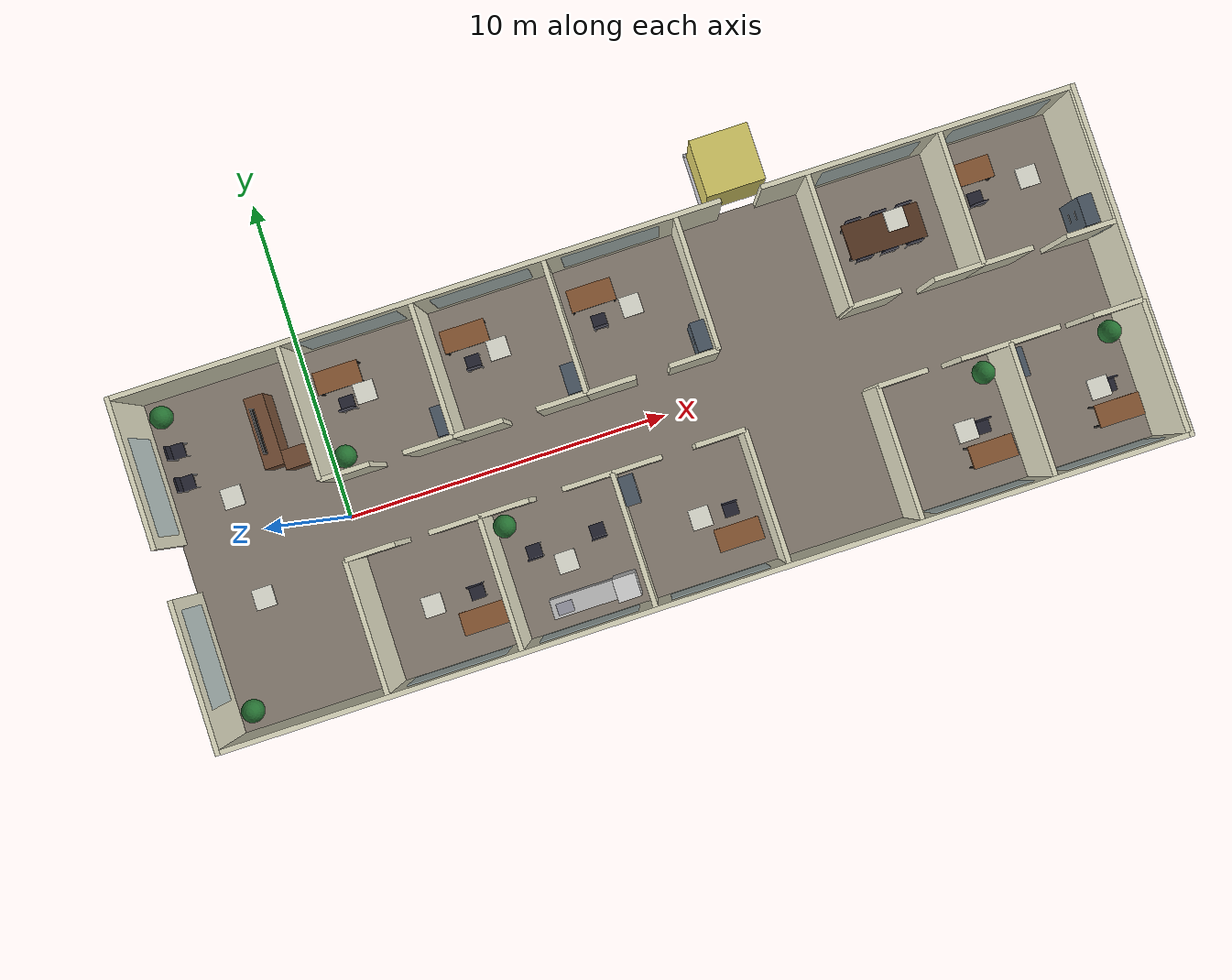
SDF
<?xml version="1.0"?>

<sdf version="1.10">

  <world name="office_world">

    <!-- PHYSICS                                           -->

    <physics name="default_physics" type="ode">

      <max_step_size>0.001</max_step_size>

      <real_time_factor>1.0</real_time_factor>

      <real_time_update_rate>1000</real_time_update_rate>

      <ode>
        <solver>
          <type>quick</type>
          <iters>150</iters>
          <sor>1.3</sor>
        </solver>
        <constraints>
          <cfm>0.0</cfm>
          <erp>0.2</erp>
          <contact_max_correcting_vel>100</contact_max_correcting_vel>
          <contact_surface_layer>0.001</contact_surface_layer>
        </constraints>
      </ode>

    </physics>

    <!-- REQUIRED SYSTEM PLUGINS                            -->

    <plugin
      filename="gz-sim-physics-system"
      name="gz::sim::systems::Physics">
    </plugin>

    <plugin
      filename="gz-sim-scene-broadcaster-system"
      name="gz::sim::systems::SceneBroadcaster">
    </plugin>

    <plugin
      filename="gz-sim-sensors-system"
      name="gz::sim::systems::Sensors">
      <render_engine>ogre2</render_engine>
    </plugin>

    <plugin
      filename="gz-sim-user-commands-system"
      name="gz::sim::systems::UserCommands">
    </plugin>

    <plugin
      filename="gz-sim-contact-system"
      name="gz::sim::systems::Contact">
    </plugin>

    <!-- GRAVITY                                           -->

    <gravity>0 0 -9.81</gravity>

    <!-- SCENE (rendering defaults for realistic look)      -->

    <scene>
      <ambient>0.6 0.6 0.6 1</ambient>
      <background>0.7 0.8 0.9 1</background>
      <shadows>true</shadows>
      <grid>false</grid>
    </scene>

    <!-- OFFICE FLOOR (structure + furniture, all nested)   -->

    <include>

      <uri>model://office_floor</uri>

      <name>office_floor</name>

      <pose>0 0 0 0 0 0</pose>

    </include>

    <!-- SUN (fill light through the windows)               -->

    <light
      name="sun"
      type="directional">

      <cast_shadows>true</cast_shadows>

      <pose>0 0 15 0 0 0</pose>

      <diffuse>1 1 1 1</diffuse>

      <specular>0.2 0.2 0.2 1</specular>

      <direction>-0.4 0.3 -1</direction>

    </light>

  </world>

</sdf>

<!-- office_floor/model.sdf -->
<!-- AUTO-GENERATED by scripts/generator/generate.py — do not hand-edit. -->

<sdf version="1.10">

  <model name="office_floor">

    <static>true</static>

    <link name="structure_link">

      <collision name="floor_0_floor_slab_collision">
        <pose>9.5000 0.0000 -0.1000 0.0000 -0.0000 0.0000</pose>
        <geometry>
          <box>
            <size>29.3000 10.7000 0.2000</size>
          </box>
        </geometry>
      </collision>
      <visual name="floor_0_floor_slab_visual">
        <pose>9.5000 0.0000 -0.1000 0.0000 -0.0000 0.0000</pose>
        <geometry>
          <box>
            <size>29.3000 10.7000 0.2000</size>
          </box>
        </geometry>
        <material>
          <ambient>0.5352970511190146 0.49679077429008417 0.45346837414708774 1</ambient>
          <diffuse>0.5352970511190146 0.49679077429008417 0.45346837414708774 1</diffuse>
          <specular>0.2 0.2 0.2 1</specular>
        </material>
      </visual>
      <collision name="floor_0_ext_wall_north_seg0_collision">
        <pose>4.2000 5.2750 1.4000 0.0000 -0.0000 0.0000</pose>
        <geometry>
          <box>
            <size>18.4000 0.1500 2.8000</size>
          </box>
        </geometry>
      </collision>
      <visual name="floor_0_ext_wall_north_seg0_visual">
        <pose>4.2000 5.2750 1.4000 0.0000 -0.0000 0.0000</pose>
        <geometry>
          <box>
            <size>18.4000 0.1500 2.8000</size>
          </box>
        </geometry>
        <material>
          <ambient>0.8777356642700563 0.866982555955925 0.7599139603924817 1</ambient>
          <diffuse>0.8777356642700563 0.866982555955925 0.7599139603924817 1</diffuse>
          <specular>0.2 0.2 0.2 1</specular>
        </material>
      </visual>
      <collision name="floor_0_ext_wall_north_seg1_collision">
        <pose>19.3000 5.2750 1.4000 0.0000 -0.0000 0.0000</pose>
        <geometry>
          <box>
            <size>9.4000 0.1500 2.8000</size>
          </box>
        </geometry>
      </collision>
      <visual name="floor_0_ext_wall_north_seg1_visual">
        <pose>19.3000 5.2750 1.4000 0.0000 -0.0000 0.0000</pose>
        <geometry>
          <box>
            <size>9.4000 0.1500 2.8000</size>
          </box>
        </geometry>
        <material>
          <ambient>0.8777356642700563 0.866982555955925 0.7599139603924817 1</ambient>
          <diffuse>0.8777356642700563 0.866982555955925 0.7599139603924817 1</diffuse>
          <specular>0.2 0.2 0.2 1</specular>
        </material>
      </visual>
      <visual name="floor_0_ext_wall_north_window_0_visual">
        <pose>2.0000 5.2000 1.4000 0.0000 -0.0000 0.0000</pose>
        <geometry>
          <box>
            <size>3.0000 0.0500 1.8000</size>
          </box>
        </geometry>
        <material>
          <ambient>0.6 0.75 0.85 1</ambient>
          <diffuse>0.6 0.75 0.85 1</diffuse>
          <specular>0.8 0.8 0.8 1</specular>
        </material>
        <transparency>0.5500</transparency>
      </visual>
      <visual name="floor_0_ext_wall_north_window_1_visual">
        <pose>6.0000 5.2000 1.4000 0.0000 -0.0000 0.0000</pose>
        <geometry>
          <box>
            <size>3.0000 0.0500 1.8000</size>
          </box>
        </geometry>
        <material>
          <ambient>0.6 0.75 0.85 1</ambient>
          <diffuse>0.6 0.75 0.85 1</diffuse>
          <specular>0.8 0.8 0.8 1</specular>
        </material>
        <transparency>0.5500</transparency>
      </visual>
      <visual name="floor_0_ext_wall_north_window_2_visual">
        <pose>10.0000 5.2000 1.4000 0.0000 -0.0000 0.0000</pose>
        <geometry>
          <box>
            <size>3.0000 0.0500 1.8000</size>
          </box>
        </geometry>
        <material>
          <ambient>0.6 0.75 0.85 1</ambient>
          <diffuse>0.6 0.75 0.85 1</diffuse>
          <specular>0.8 0.8 0.8 1</specular>
        </material>
        <transparency>0.5500</transparency>
      </visual>
      <visual name="floor_0_ext_wall_north_window_3_visual">
        <pose>18.0000 5.2000 1.4000 0.0000 -0.0000 0.0000</pose>
        <geometry>
          <box>
            <size>3.0000 0.0500 1.8000</size>
          </box>
        </geometry>
        <material>
          <ambient>0.6 0.75 0.85 1</ambient>
          <diffuse>0.6 0.75 0.85 1</diffuse>
          <specular>0.8 0.8 0.8 1</specular>
        </material>
        <transparency>0.5500</transparency>
      </visual>
      <visual name="floor_0_ext_wall_north_window_4_visual">
        <pose>22.0000 5.2000 1.4000 0.0000 -0.0000 0.0000</pose>
        <geometry>
          <box>
            <size>3.0000 0.0500 1.8000</size>
          </box>
        </geometry>
        <material>
          <ambient>0.6 0.75 0.85 1</ambient>
          <diffuse>0.6 0.75 0.85 1</diffuse>
          <specular>0.8 0.8 0.8 1</specular>
        </material>
        <transparency>0.5500</transparency>
      </visual>
      <collision name="floor_0_ext_wall_south_collision">
        <pose>9.5000 -5.2750 1.4000 0.0000 -0.0000 0.0000</pose>
        <geometry>
          <box>
            <size>29.0000 0.1500 2.8000</size>
          </box>
        </geometry>
      </collision>
      <visual name="floor_0_ext_wall_south_visual">
        <pose>9.5000 -5.2750 1.4000 0.0000 -0.0000 0.0000</pose>
        <geometry>
          <box>
            <size>29.0000 0.1500 2.8000</size>
          </box>
        </geometry>
        <material>
          <ambient>0.8777356642700563 0.866982555955925 0.7599139603924817 1</ambient>
          <diffuse>0.8777356642700563 0.866982555955925 0.7599139603924817 1</diffuse>
          <specular>0.2 0.2 0.2 1</specular>
        </material>
      </visual>
      <visual name="floor_0_ext_wall_south_window_0_visual">
        <pose>2.0000 -5.2000 1.4000 0.0000 -0.0000 0.0000</pose>
        <geometry>
          <box>
            <size>3.0000 0.0500 1.8000</size>
          </box>
        </geometry>
        <material>
          <ambient>0.6 0.75 0.85 1</ambient>
          <diffuse>0.6 0.75 0.85 1</diffuse>
          <specular>0.8 0.8 0.8 1</specular>
        </material>
        <transparency>0.5500</transparency>
      </visual>
      <visual name="floor_0_ext_wall_south_window_1_visual">
        <pose>6.0000 -5.2000 1.4000 0.0000 -0.0000 0.0000</pose>
        <geometry>
          <box>
            <size>3.0000 0.0500 1.8000</size>
          </box>
        </geometry>
        <material>
          <ambient>0.6 0.75 0.85 1</ambient>
          <diffuse>0.6 0.75 0.85 1</diffuse>
          <specular>0.8 0.8 0.8 1</specular>
        </material>
        <transparency>0.5500</transparency>
      </visual>
      <visual name="floor_0_ext_wall_south_window_2_visual">
        <pose>10.0000 -5.2000 1.4000 0.0000 -0.0000 0.0000</pose>
        <geometry>
          <box>
            <size>3.0000 0.0500 1.8000</size>
          </box>
        </geometry>
        <material>
          <ambient>0.6 0.75 0.85 1</ambient>
          <diffuse>0.6 0.75 0.85 1</diffuse>
          <specular>0.8 0.8 0.8 1</specular>
        </material>
        <transparency>0.5500</transparency>
      </visual>
      <visual name="floor_0_ext_wall_south_window_3_visual">
        <pose>18.0000 -5.2000 1.4000 0.0000 -0.0000 0.0000</pose>
        <geometry>
          <box>
            <size>3.0000 0.0500 1.8000</size>
          </box>
        </geometry>
        <material>
          <ambient>0.6 0.75 0.85 1</ambient>
          <diffuse>0.6 0.75 0.85 1</diffuse>
          <specular>0.8 0.8 0.8 1</specular>
        </material>
        <transparency>0.5500</transparency>
      </visual>
      <visual name="floor_0_ext_wall_south_window_4_visual">
        <pose>22.0000 -5.2000 1.4000 0.0000 -0.0000 0.0000</pose>
        <geometry>
          <box>
            <size>3.0000 0.0500 1.8000</size>
          </box>
        </geometry>
        <material>
          <ambient>0.6 0.75 0.85 1</ambient>
          <diffuse>0.6 0.75 0.85 1</diffuse>
          <specular>0.8 0.8 0.8 1</specular>
        </material>
        <transparency>0.5500</transparency>
      </visual>
      <collision name="floor_0_ext_wall_west_seg0_collision">
        <pose>-5.0750 -3.0500 1.4000 0.0000 -0.0000 0.0000</pose>
        <geometry>
          <box>
            <size>0.1500 4.6000 2.8000</size>
          </box>
        </geometry>
      </collision>
      <visual name="floor_0_ext_wall_west_seg0_visual">
        <pose>-5.0750 -3.0500 1.4000 0.0000 -0.0000 0.0000</pose>
        <geometry>
          <box>
            <size>0.1500 4.6000 2.8000</size>
          </box>
        </geometry>
        <material>
          <ambient>0.8777356642700563 0.866982555955925 0.7599139603924817 1</ambient>
          <diffuse>0.8777356642700563 0.866982555955925 0.7599139603924817 1</diffuse>
          <specular>0.2 0.2 0.2 1</specular>
        </material>
      </visual>
      <collision name="floor_0_ext_wall_west_seg1_collision">
        <pose>-5.0750 3.0500 1.4000 0.0000 -0.0000 0.0000</pose>
        <geometry>
          <box>
            <size>0.1500 4.6000 2.8000</size>
          </box>
        </geometry>
      </collision>
      <visual name="floor_0_ext_wall_west_seg1_visual">
        <pose>-5.0750 3.0500 1.4000 0.0000 -0.0000 0.0000</pose>
        <geometry>
          <box>
            <size>0.1500 4.6000 2.8000</size>
          </box>
        </geometry>
        <material>
          <ambient>0.8777356642700563 0.866982555955925 0.7599139603924817 1</ambient>
          <diffuse>0.8777356642700563 0.866982555955925 0.7599139603924817 1</diffuse>
          <specular>0.2 0.2 0.2 1</specular>
        </material>
      </visual>
      <visual name="floor_0_ext_wall_west_window_0_visual">
        <pose>-5.0000 2.6000 1.4000 0.0000 -0.0000 0.0000</pose>
        <geometry>
          <box>
            <size>0.0500 3.0000 1.8000</size>
          </box>
        </geometry>
        <material>
          <ambient>0.6 0.75 0.85 1</ambient>
          <diffuse>0.6 0.75 0.85 1</diffuse>
          <specular>0.8 0.8 0.8 1</specular>
        </material>
        <transparency>0.5500</transparency>
      </visual>
      <visual name="floor_0_ext_wall_west_window_1_visual">
        <pose>-5.0000 -2.6000 1.4000 0.0000 -0.0000 0.0000</pose>
        <geometry>
          <box>
            <size>0.0500 3.0000 1.8000</size>
          </box>
        </geometry>
        <material>
          <ambient>0.6 0.75 0.85 1</ambient>
          <diffuse>0.6 0.75 0.85 1</diffuse>
          <specular>0.8 0.8 0.8 1</specular>
        </material>
        <transparency>0.5500</transparency>
      </visual>
      <collision name="floor_0_ext_wall_east_collision">
        <pose>24.0750 0.0000 1.4000 0.0000 -0.0000 0.0000</pose>
        <geometry>
          <box>
            <size>0.1500 10.7000 2.8000</size>
          </box>
        </geometry>
      </collision>
      <visual name="floor_0_ext_wall_east_visual">
        <pose>24.0750 0.0000 1.4000 0.0000 -0.0000 0.0000</pose>
        <geometry>
          <box>
            <size>0.1500 10.7000 2.8000</size>
          </box>
        </geometry>
        <material>
          <ambient>0.8777356642700563 0.866982555955925 0.7599139603924817 1</ambient>
          <diffuse>0.8777356642700563 0.866982555955925 0.7599139603924817 1</diffuse>
          <specular>0.2 0.2 0.2 1</specular>
        </material>
      </visual>
      <visual name="floor_0_ext_wall_east_window_0_visual">
        <pose>24.0000 2.6000 1.4000 0.0000 -0.0000 0.0000</pose>
        <geometry>
          <box>
            <size>0.0500 3.0000 1.8000</size>
          </box>
        </geometry>
        <material>
          <ambient>0.6 0.75 0.85 1</ambient>
          <diffuse>0.6 0.75 0.85 1</diffuse>
          <specular>0.8 0.8 0.8 1</specular>
        </material>
        <transparency>0.5500</transparency>
      </visual>
      <visual name="floor_0_ext_wall_east_window_1_visual">
        <pose>24.0000 -2.6000 1.4000 0.0000 -0.0000 0.0000</pose>
        <geometry>
          <box>
            <size>0.0500 3.0000 1.8000</size>
          </box>
        </geometry>
        <material>
          <ambient>0.6 0.75 0.85 1</ambient>
          <diffuse>0.6 0.75 0.85 1</diffuse>
          <specular>0.8 0.8 0.8 1</specular>
        </material>
        <transparency>0.5500</transparency>
      </visual>
      <collision name="floor_0_corridor_wall_n_0_seg0_collision">
        <pose>0.7500 1.2000 1.4000 0.0000 -0.0000 0.0000</pose>
        <geometry>
          <box>
            <size>1.5000 0.1500 2.8000</size>
          </box>
        </geometry>
      </collision>
      <visual name="floor_0_corridor_wall_n_0_seg0_visual">
        <pose>0.7500 1.2000 1.4000 0.0000 -0.0000 0.0000</pose>
        <geometry>
          <box>
            <size>1.5000 0.1500 2.8000</size>
          </box>
        </geometry>
        <material>
          <ambient>0.8777356642700563 0.866982555955925 0.7599139603924817 1</ambient>
          <diffuse>0.8777356642700563 0.866982555955925 0.7599139603924817 1</diffuse>
          <specular>0.2 0.2 0.2 1</specular>
        </material>
      </visual>
      <collision name="floor_0_corridor_wall_n_0_seg1_collision">
        <pose>3.2500 1.2000 1.4000 0.0000 -0.0000 0.0000</pose>
        <geometry>
          <box>
            <size>1.5000 0.1500 2.8000</size>
          </box>
        </geometry>
      </collision>
      <visual name="floor_0_corridor_wall_n_0_seg1_visual">
        <pose>3.2500 1.2000 1.4000 0.0000 -0.0000 0.0000</pose>
        <geometry>
          <box>
            <size>1.5000 0.1500 2.8000</size>
          </box>
        </geometry>
        <material>
          <ambient>0.8777356642700563 0.866982555955925 0.7599139603924817 1</ambient>
          <diffuse>0.8777356642700563 0.866982555955925 0.7599139603924817 1</diffuse>
          <specular>0.2 0.2 0.2 1</specular>
        </material>
      </visual>
      <collision name="floor_0_corridor_wall_s_0_seg0_collision">
        <pose>0.7500 -1.2000 1.4000 0.0000 -0.0000 0.0000</pose>
        <geometry>
          <box>
            <size>1.5000 0.1500 2.8000</size>
          </box>
        </geometry>
      </collision>
      <visual name="floor_0_corridor_wall_s_0_seg0_visual">
        <pose>0.7500 -1.2000 1.4000 0.0000 -0.0000 0.0000</pose>
        <geometry>
          <box>
            <size>1.5000 0.1500 2.8000</size>
          </box>
        </geometry>
        <material>
          <ambient>0.8777356642700563 0.866982555955925 0.7599139603924817 1</ambient>
          <diffuse>0.8777356642700563 0.866982555955925 0.7599139603924817 1</diffuse>
          <specular>0.2 0.2 0.2 1</specular>
        </material>
      </visual>
      <collision name="floor_0_corridor_wall_s_0_seg1_collision">
        <pose>3.2500 -1.2000 1.4000 0.0000 -0.0000 0.0000</pose>
        <geometry>
          <box>
            <size>1.5000 0.1500 2.8000</size>
          </box>
        </geometry>
      </collision>
      <visual name="floor_0_corridor_wall_s_0_seg1_visual">
        <pose>3.2500 -1.2000 1.4000 0.0000 -0.0000 0.0000</pose>
        <geometry>
          <box>
            <size>1.5000 0.1500 2.8000</size>
          </box>
        </geometry>
        <material>
          <ambient>0.8777356642700563 0.866982555955925 0.7599139603924817 1</ambient>
          <diffuse>0.8777356642700563 0.866982555955925 0.7599139603924817 1</diffuse>
          <specular>0.2 0.2 0.2 1</specular>
        </material>
      </visual>
      <collision name="floor_0_corridor_wall_n_1_seg0_collision">
        <pose>4.7500 1.2000 1.4000 0.0000 -0.0000 0.0000</pose>
        <geometry>
          <box>
            <size>1.5000 0.1500 2.8000</size>
          </box>
        </geometry>
      </collision>
      <visual name="floor_0_corridor_wall_n_1_seg0_visual">
        <pose>4.7500 1.2000 1.4000 0.0000 -0.0000 0.0000</pose>
        <geometry>
          <box>
            <size>1.5000 0.1500 2.8000</size>
          </box>
        </geometry>
        <material>
          <ambient>0.8777356642700563 0.866982555955925 0.7599139603924817 1</ambient>
          <diffuse>0.8777356642700563 0.866982555955925 0.7599139603924817 1</diffuse>
          <specular>0.2 0.2 0.2 1</specular>
        </material>
      </visual>
      <collision name="floor_0_corridor_wall_n_1_seg1_collision">
        <pose>7.2500 1.2000 1.4000 0.0000 -0.0000 0.0000</pose>
        <geometry>
          <box>
            <size>1.5000 0.1500 2.8000</size>
          </box>
        </geometry>
      </collision>
      <visual name="floor_0_corridor_wall_n_1_seg1_visual">
        <pose>7.2500 1.2000 1.4000 0.0000 -0.0000 0.0000</pose>
        <geometry>
          <box>
            <size>1.5000 0.1500 2.8000</size>
          </box>
        </geometry>
        <material>
          <ambient>0.8777356642700563 0.866982555955925 0.7599139603924817 1</ambient>
          <diffuse>0.8777356642700563 0.866982555955925 0.7599139603924817 1</diffuse>
          <specular>0.2 0.2 0.2 1</specular>
        </material>
      </visual>
      <collision name="floor_0_corridor_wall_s_1_seg0_collision">
        <pose>4.7500 -1.2000 1.4000 0.0000 -0.0000 0.0000</pose>
        <geometry>
          <box>
            <size>1.5000 0.1500 2.8000</size>
          </box>
        </geometry>
      </collision>
      <visual name="floor_0_corridor_wall_s_1_seg0_visual">
        <pose>4.7500 -1.2000 1.4000 0.0000 -0.0000 0.0000</pose>
        <geometry>
          <box>
            <size>1.5000 0.1500 2.8000</size>
          </box>
        </geometry>
        <material>
          <ambient>0.8777356642700563 0.866982555955925 0.7599139603924817 1</ambient>
          <diffuse>0.8777356642700563 0.866982555955925 0.7599139603924817 1</diffuse>
          <specular>0.2 0.2 0.2 1</specular>
        </material>
      </visual>
      <collision name="floor_0_corridor_wall_s_1_seg1_collision">
        <pose>7.2500 -1.2000 1.4000 0.0000 -0.0000 0.0000</pose>
        <geometry>
          <box>
            <size>1.5000 0.1500 2.8000</size>
          </box>
        </geometry>
      </collision>
      <visual name="floor_0_corridor_wall_s_1_seg1_visual">
        <pose>7.2500 -1.2000 1.4000 0.0000 -0.0000 0.0000</pose>
        <geometry>
          <box>
            <size>1.5000 0.1500 2.8000</size>
          </box>
        </geometry>
        <material>
          <ambient>0.8777356642700563 0.866982555955925 0.7599139603924817 1</ambient>
          <diffuse>0.8777356642700563 0.866982555955925 0.7599139603924817 1</diffuse>
          <specular>0.2 0.2 0.2 1</specular>
        </material>
      </visual>
      <collision name="floor_0_corridor_wall_n_2_seg0_collision">
        <pose>8.7500 1.2000 1.4000 0.0000 -0.0000 0.0000</pose>
        <geometry>
          <box>
            <size>1.5000 0.1500 2.8000</size>
          </box>
        </geometry>
      </collision>
      <visual name="floor_0_corridor_wall_n_2_seg0_visual">
        <pose>8.7500 1.2000 1.4000 0.0000 -0.0000 0.0000</pose>
        <geometry>
          <box>
            <size>1.5000 0.1500 2.8000</size>
          </box>
        </geometry>
        <material>
          <ambient>0.8777356642700563 0.866982555955925 0.7599139603924817 1</ambient>
          <diffuse>0.8777356642700563 0.866982555955925 0.7599139603924817 1</diffuse>
          <specular>0.2 0.2 0.2 1</specular>
        </material>
      </visual>
      <collision name="floor_0_corridor_wall_n_2_seg1_collision">
        <pose>11.2500 1.2000 1.4000 0.0000 -0.0000 0.0000</pose>
        <geometry>
          <box>
            <size>1.5000 0.1500 2.8000</size>
          </box>
        </geometry>
      </collision>
      <visual name="floor_0_corridor_wall_n_2_seg1_visual">
        <pose>11.2500 1.2000 1.4000 0.0000 -0.0000 0.0000</pose>
        <geometry>
          <box>
            <size>1.5000 0.1500 2.8000</size>
          </box>
        </geometry>
        <material>
          <ambient>0.8777356642700563 0.866982555955925 0.7599139603924817 1</ambient>
          <diffuse>0.8777356642700563 0.866982555955925 0.7599139603924817 1</diffuse>
          <specular>0.2 0.2 0.2 1</specular>
        </material>
      </visual>
      <collision name="floor_0_corridor_wall_s_2_seg0_collision">
        <pose>8.7500 -1.2000 1.4000 0.0000 -0.0000 0.0000</pose>
        <geometry>
          <box>
            <size>1.5000 0.1500 2.8000</size>
          </box>
        </geometry>
      </collision>
      <visual name="floor_0_corridor_wall_s_2_seg0_visual">
        <pose>8.7500 -1.2000 1.4000 0.0000 -0.0000 0.0000</pose>
        <geometry>
          <box>
            <size>1.5000 0.1500 2.8000</size>
          </box>
        </geometry>
        <material>
          <ambient>0.8777356642700563 0.866982555955925 0.7599139603924817 1</ambient>
          <diffuse>0.8777356642700563 0.866982555955925 0.7599139603924817 1</diffuse>
          <specular>0.2 0.2 0.2 1</specular>
        </material>
      </visual>
      <collision name="floor_0_corridor_wall_s_2_seg1_collision">
        <pose>11.2500 -1.2000 1.4000 0.0000 -0.0000 0.0000</pose>
        <geometry>
          <box>
            <size>1.5000 0.1500 2.8000</size>
          </box>
        </geometry>
      </collision>
      <visual name="floor_0_corridor_wall_s_2_seg1_visual">
        <pose>11.2500 -1.2000 1.4000 0.0000 -0.0000 0.0000</pose>
        <geometry>
          <box>
            <size>1.5000 0.1500 2.8000</size>
          </box>
        </geometry>
        <material>
          <ambient>0.8777356642700563 0.866982555955925 0.7599139603924817 1</ambient>
          <diffuse>0.8777356642700563 0.866982555955925 0.7599139603924817 1</diffuse>
          <specular>0.2 0.2 0.2 1</specular>
        </material>
      </visual>
      <collision name="floor_0_corridor_wall_n_4_seg0_collision">
        <pose>16.7500 1.2000 1.4000 0.0000 -0.0000 0.0000</pose>
        <geometry>
          <box>
            <size>1.5000 0.1500 2.8000</size>
          </box>
        </geometry>
      </collision>
      <visual name="floor_0_corridor_wall_n_4_seg0_visual">
        <pose>16.7500 1.2000 1.4000 0.0000 -0.0000 0.0000</pose>
        <geometry>
          <box>
            <size>1.5000 0.1500 2.8000</size>
          </box>
        </geometry>
        <material>
          <ambient>0.8777356642700563 0.866982555955925 0.7599139603924817 1</ambient>
          <diffuse>0.8777356642700563 0.866982555955925 0.7599139603924817 1</diffuse>
          <specular>0.2 0.2 0.2 1</specular>
        </material>
      </visual>
      <collision name="floor_0_corridor_wall_n_4_seg1_collision">
        <pose>19.2500 1.2000 1.4000 0.0000 -0.0000 0.0000</pose>
        <geometry>
          <box>
            <size>1.5000 0.1500 2.8000</size>
          </box>
        </geometry>
      </collision>
      <visual name="floor_0_corridor_wall_n_4_seg1_visual">
        <pose>19.2500 1.2000 1.4000 0.0000 -0.0000 0.0000</pose>
        <geometry>
          <box>
            <size>1.5000 0.1500 2.8000</size>
          </box>
        </geometry>
        <material>
          <ambient>0.8777356642700563 0.866982555955925 0.7599139603924817 1</ambient>
          <diffuse>0.8777356642700563 0.866982555955925 0.7599139603924817 1</diffuse>
          <specular>0.2 0.2 0.2 1</specular>
        </material>
      </visual>
      <collision name="floor_0_corridor_wall_s_4_seg0_collision">
        <pose>16.7500 -1.2000 1.4000 0.0000 -0.0000 0.0000</pose>
        <geometry>
          <box>
            <size>1.5000 0.1500 2.8000</size>
          </box>
        </geometry>
      </collision>
      <visual name="floor_0_corridor_wall_s_4_seg0_visual">
        <pose>16.7500 -1.2000 1.4000 0.0000 -0.0000 0.0000</pose>
        <geometry>
          <box>
            <size>1.5000 0.1500 2.8000</size>
          </box>
        </geometry>
        <material>
          <ambient>0.8777356642700563 0.866982555955925 0.7599139603924817 1</ambient>
          <diffuse>0.8777356642700563 0.866982555955925 0.7599139603924817 1</diffuse>
          <specular>0.2 0.2 0.2 1</specular>
        </material>
      </visual>
      <collision name="floor_0_corridor_wall_s_4_seg1_collision">
        <pose>19.2500 -1.2000 1.4000 0.0000 -0.0000 0.0000</pose>
        <geometry>
          <box>
            <size>1.5000 0.1500 2.8000</size>
          </box>
        </geometry>
      </collision>
      <visual name="floor_0_corridor_wall_s_4_seg1_visual">
        <pose>19.2500 -1.2000 1.4000 0.0000 -0.0000 0.0000</pose>
        <geometry>
          <box>
            <size>1.5000 0.1500 2.8000</size>
          </box>
        </geometry>
        <material>
          <ambient>0.8777356642700563 0.866982555955925 0.7599139603924817 1</ambient>
          <diffuse>0.8777356642700563 0.866982555955925 0.7599139603924817 1</diffuse>
          <specular>0.2 0.2 0.2 1</specular>
        </material>
      </visual>
      <collision name="floor_0_corridor_wall_n_5_seg0_collision">
        <pose>20.7500 1.2000 1.4000 0.0000 -0.0000 0.0000</pose>
        <geometry>
          <box>
            <size>1.5000 0.1500 2.8000</size>
          </box>
        </geometry>
      </collision>
      <visual name="floor_0_corridor_wall_n_5_seg0_visual">
        <pose>20.7500 1.2000 1.4000 0.0000 -0.0000 0.0000</pose>
        <geometry>
          <box>
            <size>1.5000 0.1500 2.8000</size>
          </box>
        </geometry>
        <material>
          <ambient>0.8777356642700563 0.866982555955925 0.7599139603924817 1</ambient>
          <diffuse>0.8777356642700563 0.866982555955925 0.7599139603924817 1</diffuse>
          <specular>0.2 0.2 0.2 1</specular>
        </material>
      </visual>
      <collision name="floor_0_corridor_wall_n_5_seg1_collision">
        <pose>23.2500 1.2000 1.4000 0.0000 -0.0000 0.0000</pose>
        <geometry>
          <box>
            <size>1.5000 0.1500 2.8000</size>
          </box>
        </geometry>
      </collision>
      <visual name="floor_0_corridor_wall_n_5_seg1_visual">
        <pose>23.2500 1.2000 1.4000 0.0000 -0.0000 0.0000</pose>
        <geometry>
          <box>
            <size>1.5000 0.1500 2.8000</size>
          </box>
        </geometry>
        <material>
          <ambient>0.8777356642700563 0.866982555955925 0.7599139603924817 1</ambient>
          <diffuse>0.8777356642700563 0.866982555955925 0.7599139603924817 1</diffuse>
          <specular>0.2 0.2 0.2 1</specular>
        </material>
      </visual>
      <collision name="floor_0_corridor_wall_s_5_seg0_collision">
        <pose>20.7500 -1.2000 1.4000 0.0000 -0.0000 0.0000</pose>
        <geometry>
          <box>
            <size>1.5000 0.1500 2.8000</size>
          </box>
        </geometry>
      </collision>
      <visual name="floor_0_corridor_wall_s_5_seg0_visual">
        <pose>20.7500 -1.2000 1.4000 0.0000 -0.0000 0.0000</pose>
        <geometry>
          <box>
            <size>1.5000 0.1500 2.8000</size>
          </box>
        </geometry>
        <material>
          <ambient>0.8777356642700563 0.866982555955925 0.7599139603924817 1</ambient>
          <diffuse>0.8777356642700563 0.866982555955925 0.7599139603924817 1</diffuse>
          <specular>0.2 0.2 0.2 1</specular>
        </material>
      </visual>
      <collision name="floor_0_corridor_wall_s_5_seg1_collision">
        <pose>23.2500 -1.2000 1.4000 0.0000 -0.0000 0.0000</pose>
        <geometry>
          <box>
            <size>1.5000 0.1500 2.8000</size>
          </box>
        </geometry>
      </collision>
      <visual name="floor_0_corridor_wall_s_5_seg1_visual">
        <pose>23.2500 -1.2000 1.4000 0.0000 -0.0000 0.0000</pose>
        <geometry>
          <box>
            <size>1.5000 0.1500 2.8000</size>
          </box>
        </geometry>
        <material>
          <ambient>0.8777356642700563 0.866982555955925 0.7599139603924817 1</ambient>
          <diffuse>0.8777356642700563 0.866982555955925 0.7599139603924817 1</diffuse>
          <specular>0.2 0.2 0.2 1</specular>
        </material>
      </visual>
      <collision name="floor_0_partition_n_0_collision">
        <pose>0.0000 3.2000 1.4000 0.0000 -0.0000 0.0000</pose>
        <geometry>
          <box>
            <size>0.1500 4.0000 2.8000</size>
          </box>
        </geometry>
      </collision>
      <visual name="floor_0_partition_n_0_visual">
        <pose>0.0000 3.2000 1.4000 0.0000 -0.0000 0.0000</pose>
        <geometry>
          <box>
            <size>0.1500 4.0000 2.8000</size>
          </box>
        </geometry>
        <material>
          <ambient>0.8777356642700563 0.866982555955925 0.7599139603924817 1</ambient>
          <diffuse>0.8777356642700563 0.866982555955925 0.7599139603924817 1</diffuse>
          <specular>0.2 0.2 0.2 1</specular>
        </material>
      </visual>
      <collision name="floor_0_partition_s_0_collision">
        <pose>0.0000 -3.2000 1.4000 0.0000 -0.0000 0.0000</pose>
        <geometry>
          <box>
            <size>0.1500 4.0000 2.8000</size>
          </box>
        </geometry>
      </collision>
      <visual name="floor_0_partition_s_0_visual">
        <pose>0.0000 -3.2000 1.4000 0.0000 -0.0000 0.0000</pose>
        <geometry>
          <box>
            <size>0.1500 4.0000 2.8000</size>
          </box>
        </geometry>
        <material>
          <ambient>0.8777356642700563 0.866982555955925 0.7599139603924817 1</ambient>
          <diffuse>0.8777356642700563 0.866982555955925 0.7599139603924817 1</diffuse>
          <specular>0.2 0.2 0.2 1</specular>
        </material>
      </visual>
      <collision name="floor_0_partition_n_1_collision">
        <pose>4.0000 3.2000 1.4000 0.0000 -0.0000 0.0000</pose>
        <geometry>
          <box>
            <size>0.1500 4.0000 2.8000</size>
          </box>
        </geometry>
      </collision>
      <visual name="floor_0_partition_n_1_visual">
        <pose>4.0000 3.2000 1.4000 0.0000 -0.0000 0.0000</pose>
        <geometry>
          <box>
            <size>0.1500 4.0000 2.8000</size>
          </box>
        </geometry>
        <material>
          <ambient>0.8777356642700563 0.866982555955925 0.7599139603924817 1</ambient>
          <diffuse>0.8777356642700563 0.866982555955925 0.7599139603924817 1</diffuse>
          <specular>0.2 0.2 0.2 1</specular>
        </material>
      </visual>
      <collision name="floor_0_partition_s_1_collision">
        <pose>4.0000 -3.2000 1.4000 0.0000 -0.0000 0.0000</pose>
        <geometry>
          <box>
            <size>0.1500 4.0000 2.8000</size>
          </box>
        </geometry>
      </collision>
      <visual name="floor_0_partition_s_1_visual">
        <pose>4.0000 -3.2000 1.4000 0.0000 -0.0000 0.0000</pose>
        <geometry>
          <box>
            <size>0.1500 4.0000 2.8000</size>
          </box>
        </geometry>
        <material>
          <ambient>0.8777356642700563 0.866982555955925 0.7599139603924817 1</ambient>
          <diffuse>0.8777356642700563 0.866982555955925 0.7599139603924817 1</diffuse>
          <specular>0.2 0.2 0.2 1</specular>
        </material>
      </visual>
      <collision name="floor_0_partition_n_2_collision">
        <pose>8.0000 3.2000 1.4000 0.0000 -0.0000 0.0000</pose>
        <geometry>
          <box>
            <size>0.1500 4.0000 2.8000</size>
          </box>
        </geometry>
      </collision>
      <visual name="floor_0_partition_n_2_visual">
        <pose>8.0000 3.2000 1.4000 0.0000 -0.0000 0.0000</pose>
        <geometry>
          <box>
            <size>0.1500 4.0000 2.8000</size>
          </box>
        </geometry>
        <material>
          <ambient>0.8777356642700563 0.866982555955925 0.7599139603924817 1</ambient>
          <diffuse>0.8777356642700563 0.866982555955925 0.7599139603924817 1</diffuse>
          <specular>0.2 0.2 0.2 1</specular>
        </material>
      </visual>
      <collision name="floor_0_partition_s_2_collision">
        <pose>8.0000 -3.2000 1.4000 0.0000 -0.0000 0.0000</pose>
        <geometry>
          <box>
            <size>0.1500 4.0000 2.8000</size>
          </box>
        </geometry>
      </collision>
      <visual name="floor_0_partition_s_2_visual">
        <pose>8.0000 -3.2000 1.4000 0.0000 -0.0000 0.0000</pose>
        <geometry>
          <box>
            <size>0.1500 4.0000 2.8000</size>
          </box>
        </geometry>
        <material>
          <ambient>0.8777356642700563 0.866982555955925 0.7599139603924817 1</ambient>
          <diffuse>0.8777356642700563 0.866982555955925 0.7599139603924817 1</diffuse>
          <specular>0.2 0.2 0.2 1</specular>
        </material>
      </visual>
      <collision name="floor_0_partition_n_3_collision">
        <pose>12.0000 3.2000 1.4000 0.0000 -0.0000 0.0000</pose>
        <geometry>
          <box>
            <size>0.1500 4.0000 2.8000</size>
          </box>
        </geometry>
      </collision>
      <visual name="floor_0_partition_n_3_visual">
        <pose>12.0000 3.2000 1.4000 0.0000 -0.0000 0.0000</pose>
        <geometry>
          <box>
            <size>0.1500 4.0000 2.8000</size>
          </box>
        </geometry>
        <material>
          <ambient>0.8777356642700563 0.866982555955925 0.7599139603924817 1</ambient>
          <diffuse>0.8777356642700563 0.866982555955925 0.7599139603924817 1</diffuse>
          <specular>0.2 0.2 0.2 1</specular>
        </material>
      </visual>
      <collision name="floor_0_partition_s_3_collision">
        <pose>12.0000 -3.2000 1.4000 0.0000 -0.0000 0.0000</pose>
        <geometry>
          <box>
            <size>0.1500 4.0000 2.8000</size>
          </box>
        </geometry>
      </collision>
      <visual name="floor_0_partition_s_3_visual">
        <pose>12.0000 -3.2000 1.4000 0.0000 -0.0000 0.0000</pose>
        <geometry>
          <box>
            <size>0.1500 4.0000 2.8000</size>
          </box>
        </geometry>
        <material>
          <ambient>0.8777356642700563 0.866982555955925 0.7599139603924817 1</ambient>
          <diffuse>0.8777356642700563 0.866982555955925 0.7599139603924817 1</diffuse>
          <specular>0.2 0.2 0.2 1</specular>
        </material>
      </visual>
      <collision name="floor_0_partition_n_4_collision">
        <pose>16.0000 3.2000 1.4000 0.0000 -0.0000 0.0000</pose>
        <geometry>
          <box>
            <size>0.1500 4.0000 2.8000</size>
          </box>
        </geometry>
      </collision>
      <visual name="floor_0_partition_n_4_visual">
        <pose>16.0000 3.2000 1.4000 0.0000 -0.0000 0.0000</pose>
        <geometry>
          <box>
            <size>0.1500 4.0000 2.8000</size>
          </box>
        </geometry>
        <material>
          <ambient>0.8777356642700563 0.866982555955925 0.7599139603924817 1</ambient>
          <diffuse>0.8777356642700563 0.866982555955925 0.7599139603924817 1</diffuse>
          <specular>0.2 0.2 0.2 1</specular>
        </material>
      </visual>
      <collision name="floor_0_partition_s_4_collision">
        <pose>16.0000 -3.2000 1.4000 0.0000 -0.0000 0.0000</pose>
        <geometry>
          <box>
            <size>0.1500 4.0000 2.8000</size>
          </box>
        </geometry>
      </collision>
      <visual name="floor_0_partition_s_4_visual">
        <pose>16.0000 -3.2000 1.4000 0.0000 -0.0000 0.0000</pose>
        <geometry>
          <box>
            <size>0.1500 4.0000 2.8000</size>
          </box>
        </geometry>
        <material>
          <ambient>0.8777356642700563 0.866982555955925 0.7599139603924817 1</ambient>
          <diffuse>0.8777356642700563 0.866982555955925 0.7599139603924817 1</diffuse>
          <specular>0.2 0.2 0.2 1</specular>
        </material>
      </visual>
      <collision name="floor_0_partition_n_5_collision">
        <pose>20.0000 3.2000 1.4000 0.0000 -0.0000 0.0000</pose>
        <geometry>
          <box>
            <size>0.1500 4.0000 2.8000</size>
          </box>
        </geometry>
      </collision>
      <visual name="floor_0_partition_n_5_visual">
        <pose>20.0000 3.2000 1.4000 0.0000 -0.0000 0.0000</pose>
        <geometry>
          <box>
            <size>0.1500 4.0000 2.8000</size>
          </box>
        </geometry>
        <material>
          <ambient>0.8777356642700563 0.866982555955925 0.7599139603924817 1</ambient>
          <diffuse>0.8777356642700563 0.866982555955925 0.7599139603924817 1</diffuse>
          <specular>0.2 0.2 0.2 1</specular>
        </material>
      </visual>
      <collision name="floor_0_partition_s_5_collision">
        <pose>20.0000 -3.2000 1.4000 0.0000 -0.0000 0.0000</pose>
        <geometry>
          <box>
            <size>0.1500 4.0000 2.8000</size>
          </box>
        </geometry>
      </collision>
      <visual name="floor_0_partition_s_5_visual">
        <pose>20.0000 -3.2000 1.4000 0.0000 -0.0000 0.0000</pose>
        <geometry>
          <box>
            <size>0.1500 4.0000 2.8000</size>
          </box>
        </geometry>
        <material>
          <ambient>0.8777356642700563 0.866982555955925 0.7599139603924817 1</ambient>
          <diffuse>0.8777356642700563 0.866982555955925 0.7599139603924817 1</diffuse>
          <specular>0.2 0.2 0.2 1</specular>
        </material>
      </visual>
      <collision name="floor_0_partition_n_6_collision">
        <pose>24.0000 3.2000 1.4000 0.0000 -0.0000 0.0000</pose>
        <geometry>
          <box>
            <size>0.1500 4.0000 2.8000</size>
          </box>
        </geometry>
      </collision>
      <visual name="floor_0_partition_n_6_visual">
        <pose>24.0000 3.2000 1.4000 0.0000 -0.0000 0.0000</pose>
        <geometry>
          <box>
            <size>0.1500 4.0000 2.8000</size>
          </box>
        </geometry>
        <material>
          <ambient>0.8777356642700563 0.866982555955925 0.7599139603924817 1</ambient>
          <diffuse>0.8777356642700563 0.866982555955925 0.7599139603924817 1</diffuse>
          <specular>0.2 0.2 0.2 1</specular>
        </material>
      </visual>
      <collision name="floor_0_partition_s_6_collision">
        <pose>24.0000 -3.2000 1.4000 0.0000 -0.0000 0.0000</pose>
        <geometry>
          <box>
            <size>0.1500 4.0000 2.8000</size>
          </box>
        </geometry>
      </collision>
      <visual name="floor_0_partition_s_6_visual">
        <pose>24.0000 -3.2000 1.4000 0.0000 -0.0000 0.0000</pose>
        <geometry>
          <box>
            <size>0.1500 4.0000 2.8000</size>
          </box>
        </geometry>
        <material>
          <ambient>0.8777356642700563 0.866982555955925 0.7599139603924817 1</ambient>
          <diffuse>0.8777356642700563 0.866982555955925 0.7599139603924817 1</diffuse>
          <specular>0.2 0.2 0.2 1</specular>
        </material>
      </visual>
      <collision name="floor_0_elevator_wall_back_collision">
        <pose>14.0000 7.3750 0.0000 0.0000 -0.0000 0.0000</pose>
        <geometry>
          <box>
            <size>2.0000 0.1500 0.0000</size>
          </box>
        </geometry>
      </collision>
      <visual name="floor_0_elevator_wall_back_visual">
        <pose>14.0000 7.3750 0.0000 0.0000 -0.0000 0.0000</pose>
        <geometry>
          <box>
            <size>2.0000 0.1500 0.0000</size>
          </box>
        </geometry>
        <material>
          <ambient>0.75 0.75 0.78 1</ambient>
          <diffuse>0.75 0.75 0.78 1</diffuse>
          <specular>0.2 0.2 0.2 1</specular>
        </material>
      </visual>
      <collision name="floor_0_elevator_wall_left_collision">
        <pose>13.0750 6.4500 0.0000 0.0000 -0.0000 0.0000</pose>
        <geometry>
          <box>
            <size>0.1500 2.0000 0.0000</size>
          </box>
        </geometry>
      </collision>
      <visual name="floor_0_elevator_wall_left_visual">
        <pose>13.0750 6.4500 0.0000 0.0000 -0.0000 0.0000</pose>
        <geometry>
          <box>
            <size>0.1500 2.0000 0.0000</size>
          </box>
        </geometry>
        <material>
          <ambient>0.75 0.75 0.78 1</ambient>
          <diffuse>0.75 0.75 0.78 1</diffuse>
          <specular>0.2 0.2 0.2 1</specular>
        </material>
      </visual>
      <collision name="floor_0_elevator_wall_right_collision">
        <pose>14.9250 6.4500 0.0000 0.0000 -0.0000 0.0000</pose>
        <geometry>
          <box>
            <size>0.1500 2.0000 0.0000</size>
          </box>
        </geometry>
      </collision>
      <visual name="floor_0_elevator_wall_right_visual">
        <pose>14.9250 6.4500 0.0000 0.0000 -0.0000 0.0000</pose>
        <geometry>
          <box>
            <size>0.1500 2.0000 0.0000</size>
          </box>
        </geometry>
        <material>
          <ambient>0.75 0.75 0.78 1</ambient>
          <diffuse>0.75 0.75 0.78 1</diffuse>
          <specular>0.2 0.2 0.2 1</specular>
        </material>
      </visual>
      <collision name="floor_0_elevator_cabin_collision">
        <pose>14.0000 6.4500 1.1000 0.0000 -0.0000 0.0000</pose>
        <geometry>
          <box>
            <size>1.8000 1.7500 2.2000</size>
          </box>
        </geometry>
      </collision>
      <visual name="floor_0_elevator_cabin_visual">
        <pose>14.0000 6.4500 1.1000 0.0000 -0.0000 0.0000</pose>
        <geometry>
          <box>
            <size>1.8000 1.7500 2.2000</size>
          </box>
        </geometry>
        <material>
          <ambient>0.85 0.8 0.4 1</ambient>
          <diffuse>0.85 0.8 0.4 1</diffuse>
          <specular>0.2 0.2 0.2 1</specular>
        </material>
      </visual>
    </link>

    <include>
      <uri>model://office_desk</uri>
      <name>floor_0_office_n_0_desk</name>
      <pose>1.0000 4.1000 0.0000 0.0000 -0.0000 0.0000</pose>
    </include>
    <include>
      <uri>model://office_chair</uri>
      <name>floor_0_office_n_0_chair</name>
      <pose>1.0000 3.3000 0.0000 0.0000 -0.0000 0.0000</pose>
    </include>
    <include>
      <uri>model://office_cabinet</uri>
      <name>floor_0_office_n_0_cabinet</name>
      <pose>3.9250 1.8250 0.0000 0.0000 -0.0000 -1.5708</pose>
    </include>
    <include>
      <uri>model://ceiling_light</uri>
      <name>floor_0_office_n_0_light</name>
      <pose>2.0000 3.2000 2.7500 0.0000 -0.0000 0.0000</pose>
    </include>
    <include>
      <uri>model://potted_plant</uri>
      <name>floor_0_office_n_0_plant</name>
      <pose>0.5000 1.7750 0.0000 0.0000 -0.0000 0.0000</pose>
    </include>
    <include>
      <uri>model://office_desk</uri>
      <name>floor_0_office_s_0_desk</name>
      <pose>3.0000 -4.1000 0.0000 0.0000 -0.0000 -3.1416</pose>
    </include>
    <include>
      <uri>model://office_chair</uri>
      <name>floor_0_office_s_0_chair</name>
      <pose>3.0000 -3.3000 0.0000 0.0000 -0.0000 -3.1416</pose>
    </include>
    <include>
      <uri>model://ceiling_light</uri>
      <name>floor_0_office_s_0_light</name>
      <pose>2.0000 -3.2000 2.7500 0.0000 -0.0000 -3.1416</pose>
    </include>
    <include>
      <uri>model://office_desk</uri>
      <name>floor_0_office_n_1_desk</name>
      <pose>5.0000 4.1000 0.0000 0.0000 -0.0000 0.0000</pose>
    </include>
    <include>
      <uri>model://office_chair</uri>
      <name>floor_0_office_n_1_chair</name>
      <pose>5.0000 3.3000 0.0000 0.0000 -0.0000 0.0000</pose>
    </include>
    <include>
      <uri>model://office_cabinet</uri>
      <name>floor_0_office_n_1_cabinet</name>
      <pose>7.9250 1.8250 0.0000 0.0000 -0.0000 -1.5708</pose>
    </include>
    <include>
      <uri>model://ceiling_light</uri>
      <name>floor_0_office_n_1_light</name>
      <pose>6.0000 3.2000 2.7500 0.0000 -0.0000 0.0000</pose>
    </include>
    <include>
      <uri>model://break_counter</uri>
      <name>floor_0_break_room_counter</name>
      <pose>6.0000 -4.5000 0.0000 0.0000 -0.0000 -3.1416</pose>
    </include>
    <include>
      <uri>model://office_chair</uri>
      <name>floor_0_break_room_chair_0</name>
      <pose>7.0000 -2.7000 0.0000 0.0000 -0.0000 0.0000</pose>
    </include>
    <include>
      <uri>model://office_chair</uri>
      <name>floor_0_break_room_chair_1</name>
      <pose>5.0000 -2.7000 0.0000 0.0000 -0.0000 0.0000</pose>
    </include>
    <include>
      <uri>model://potted_plant</uri>
      <name>floor_0_break_room_plant</name>
      <pose>4.4000 -1.7000 0.0000 0.0000 -0.0000 -3.1416</pose>
    </include>
    <include>
      <uri>model://ceiling_light</uri>
      <name>floor_0_break_room_light</name>
      <pose>6.0000 -3.2000 2.7500 0.0000 -0.0000 -3.1416</pose>
    </include>
    <include>
      <uri>model://office_desk</uri>
      <name>floor_0_office_n_2_desk</name>
      <pose>9.0000 4.1000 0.0000 0.0000 -0.0000 0.0000</pose>
    </include>
    <include>
      <uri>model://office_chair</uri>
      <name>floor_0_office_n_2_chair</name>
      <pose>9.0000 3.3000 0.0000 0.0000 -0.0000 0.0000</pose>
    </include>
    <include>
      <uri>model://office_cabinet</uri>
      <name>floor_0_office_n_2_cabinet</name>
      <pose>11.9250 1.8250 0.0000 0.0000 -0.0000 -1.5708</pose>
    </include>
    <include>
      <uri>model://ceiling_light</uri>
      <name>floor_0_office_n_2_light</name>
      <pose>10.0000 3.2000 2.7500 0.0000 -0.0000 0.0000</pose>
    </include>
    <include>
      <uri>model://office_desk</uri>
      <name>floor_0_office_s_2_desk</name>
      <pose>11.0000 -4.1000 0.0000 0.0000 -0.0000 -3.1416</pose>
    </include>
    <include>
      <uri>model://office_chair</uri>
      <name>floor_0_office_s_2_chair</name>
      <pose>11.0000 -3.3000 0.0000 0.0000 -0.0000 -3.1416</pose>
    </include>
    <include>
      <uri>model://office_cabinet</uri>
      <name>floor_0_office_s_2_cabinet</name>
      <pose>8.0750 -1.8250 0.0000 0.0000 -0.0000 1.5708</pose>
    </include>
    <include>
      <uri>model://ceiling_light</uri>
      <name>floor_0_office_s_2_light</name>
      <pose>10.0000 -3.2000 2.7500 0.0000 -0.0000 -3.1416</pose>
    </include>
    <include>
      <uri>model://meeting_table</uri>
      <name>floor_0_meeting_room_table</name>
      <pose>18.0000 3.2000 0.0000 0.0000 -0.0000 0.0000</pose>
    </include>
    <include>
      <uri>model://office_chair</uri>
      <name>floor_0_meeting_room_chair_0</name>
      <pose>17.2000 3.6000 0.0000 0.0000 -0.0000 3.1416</pose>
    </include>
    <include>
      <uri>model://office_chair</uri>
      <name>floor_0_meeting_room_chair_1</name>
      <pose>18.0000 3.6000 0.0000 0.0000 -0.0000 3.1416</pose>
    </include>
    <include>
      <uri>model://office_chair</uri>
      <name>floor_0_meeting_room_chair_2</name>
      <pose>18.8000 3.6000 0.0000 0.0000 -0.0000 3.1416</pose>
    </include>
    <include>
      <uri>model://office_chair</uri>
      <name>floor_0_meeting_room_chair_3</name>
      <pose>17.2000 2.8000 0.0000 0.0000 -0.0000 0.0000</pose>
    </include>
    <include>
      <uri>model://office_chair</uri>
      <name>floor_0_meeting_room_chair_4</name>
      <pose>18.0000 2.8000 0.0000 0.0000 -0.0000 0.0000</pose>
    </include>
    <include>
      <uri>model://office_chair</uri>
      <name>floor_0_meeting_room_chair_5</name>
      <pose>18.8000 2.8000 0.0000 0.0000 -0.0000 0.0000</pose>
    </include>
    <include>
      <uri>model://ceiling_light</uri>
      <name>floor_0_meeting_room_light</name>
      <pose>18.0000 3.2000 2.7500 0.0000 -0.0000 0.0000</pose>
    </include>
    <include>
      <uri>model://office_desk</uri>
      <name>floor_0_office_s_4_desk</name>
      <pose>19.0000 -4.1000 0.0000 0.0000 -0.0000 -3.1416</pose>
    </include>
    <include>
      <uri>model://office_chair</uri>
      <name>floor_0_office_s_4_chair</name>
      <pose>19.0000 -3.3000 0.0000 0.0000 -0.0000 -3.1416</pose>
    </include>
    <include>
      <uri>model://ceiling_light</uri>
      <name>floor_0_office_s_4_light</name>
      <pose>18.0000 -3.2000 2.7500 0.0000 -0.0000 -3.1416</pose>
    </include>
    <include>
      <uri>model://potted_plant</uri>
      <name>floor_0_office_s_4_plant</name>
      <pose>19.5000 -1.7750 0.0000 0.0000 -0.0000 -3.1416</pose>
    </include>
    <include>
      <uri>model://office_desk</uri>
      <name>floor_0_office_n_5_desk</name>
      <pose>21.0000 4.1000 0.0000 0.0000 -0.0000 0.0000</pose>
    </include>
    <include>
      <uri>model://office_chair</uri>
      <name>floor_0_office_n_5_chair</name>
      <pose>21.0000 3.3000 0.0000 0.0000 -0.0000 0.0000</pose>
    </include>
    <include>
      <uri>model://office_cabinet</uri>
      <name>floor_0_office_n_5_cabinet</name>
      <pose>23.9250 1.8250 0.0000 0.0000 -0.0000 -1.5708</pose>
    </include>
    <include>
      <uri>model://ceiling_light</uri>
      <name>floor_0_office_n_5_light</name>
      <pose>22.0000 3.2000 2.7500 0.0000 -0.0000 0.0000</pose>
    </include>
    <include>
      <uri>model://office_desk</uri>
      <name>floor_0_office_s_5_desk</name>
      <pose>23.0000 -4.1000 0.0000 0.0000 -0.0000 -3.1416</pose>
    </include>
    <include>
      <uri>model://office_chair</uri>
      <name>floor_0_office_s_5_chair</name>
      <pose>23.0000 -3.3000 0.0000 0.0000 -0.0000 -3.1416</pose>
    </include>
    <include>
      <uri>model://office_cabinet</uri>
      <name>floor_0_office_s_5_cabinet</name>
      <pose>20.0750 -1.8250 0.0000 0.0000 -0.0000 1.5708</pose>
    </include>
    <include>
      <uri>model://ceiling_light</uri>
      <name>floor_0_office_s_5_light</name>
      <pose>22.0000 -3.2000 2.7500 0.0000 -0.0000 -3.1416</pose>
    </include>
    <include>
      <uri>model://potted_plant</uri>
      <name>floor_0_office_s_5_plant</name>
      <pose>23.5000 -1.7750 0.0000 0.0000 -0.0000 -3.1416</pose>
    </include>
    <include>
      <uri>model://reception_desk</uri>
      <name>floor_0_lobby_reception_desk</name>
      <pose>-1.5000 3.2000 0.0000 0.0000 -0.0000 1.5708</pose>
    </include>
    <include>
      <uri>model://office_chair</uri>
      <name>floor_0_lobby_chair_0</name>
      <pose>-4.3000 3.5000 0.0000 0.0000 -0.0000 -1.5708</pose>
    </include>
    <include>
      <uri>model://office_chair</uri>
      <name>floor_0_lobby_chair_1</name>
      <pose>-4.3000 2.5000 0.0000 0.0000 -0.0000 -1.5708</pose>
    </include>
    <include>
      <uri>model://potted_plant</uri>
      <name>floor_0_lobby_plant_0</name>
      <pose>-4.4000 4.6000 0.0000 0.0000 -0.0000 0.0000</pose>
    </include>
    <include>
      <uri>model://potted_plant</uri>
      <name>floor_0_lobby_plant_1</name>
      <pose>-4.4000 -4.6000 0.0000 0.0000 -0.0000 0.0000</pose>
    </include>
    <include>
      <uri>model://ceiling_light</uri>
      <name>floor_0_lobby_light_0</name>
      <pose>-2.5000 1.5000 2.7500 0.0000 -0.0000 0.0000</pose>
    </include>
    <include>
      <uri>model://ceiling_light</uri>
      <name>floor_0_lobby_light_1</name>
      <pose>-2.5000 -1.5000 2.7500 0.0000 -0.0000 0.0000</pose>
    </include>
  </model>

</sdf>

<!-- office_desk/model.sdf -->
<sdf version="1.10">

  <model name="office_desk">

    <static>true</static>

    <link name="desk_link">

      <!-- DESK TOP                    -->

      <collision name="top_collision">

        <pose>0 0 0.72 0 0 0</pose>

        <geometry>
          <box>
            <size>1.4 0.7 0.05</size>
          </box>
        </geometry>

      </collision>

      <visual name="top_visual">

        <pose>0 0 0.72 0 0 0</pose>

        <geometry>
          <box>
            <size>1.4 0.7 0.05</size>
          </box>
        </geometry>

        <material>
          <ambient>0.55 0.35 0.2 1</ambient>
          <diffuse>0.55 0.35 0.2 1</diffuse>
          <specular>0.2 0.2 0.2 1</specular>
        </material>

      </visual>

      <!-- LEG 1                      -->

      <collision name="leg_1_collision">
        <pose>0.65 0.3 0.35 0 0 0</pose>
        <geometry>
          <box>
            <size>0.05 0.05 0.7</size>
          </box>
        </geometry>
      </collision>

      <visual name="leg_1_visual">
        <pose>0.65 0.3 0.35 0 0 0</pose>
        <geometry>
          <box>
            <size>0.05 0.05 0.7</size>
          </box>
        </geometry>
        <material>
          <ambient>0.2 0.2 0.2 1</ambient>
          <diffuse>0.2 0.2 0.2 1</diffuse>
        </material>
      </visual>

      <!-- LEG 2                      -->

      <collision name="leg_2_collision">
        <pose>-0.65 0.3 0.35 0 0 0</pose>
        <geometry>
          <box>
            <size>0.05 0.05 0.7</size>
          </box>
        </geometry>
      </collision>

      <visual name="leg_2_visual">
        <pose>-0.65 0.3 0.35 0 0 0</pose>
        <geometry>
          <box>
            <size>0.05 0.05 0.7</size>
          </box>
        </geometry>
        <material>
          <ambient>0.2 0.2 0.2 1</ambient>
          <diffuse>0.2 0.2 0.2 1</diffuse>
        </material>
      </visual>

      <!-- LEG 3                      -->

      <collision name="leg_3_collision">
        <pose>0.65 -0.3 0.35 0 0 0</pose>
        <geometry>
          <box>
            <size>0.05 0.05 0.7</size>
          </box>
        </geometry>
      </collision>

      <visual name="leg_3_visual">
        <pose>0.65 -0.3 0.35 0 0 0</pose>
        <geometry>
          <box>
            <size>0.05 0.05 0.7</size>
          </box>
        </geometry>
        <material>
          <ambient>0.2 0.2 0.2 1</ambient>
          <diffuse>0.2 0.2 0.2 1</diffuse>
        </material>
      </visual>

      <!-- LEG 4                      -->

      <collision name="leg_4_collision">
        <pose>-0.65 -0.3 0.35 0 0 0</pose>
        <geometry>
          <box>
            <size>0.05 0.05 0.7</size>
          </box>
        </geometry>
      </collision>

      <visual name="leg_4_visual">
        <pose>-0.65 -0.3 0.35 0 0 0</pose>
        <geometry>
          <box>
            <size>0.05 0.05 0.7</size>
          </box>
        </geometry>
        <material>
          <ambient>0.2 0.2 0.2 1</ambient>
          <diffuse>0.2 0.2 0.2 1</diffuse>
        </material>
      </visual>

    </link>

  </model>

</sdf>

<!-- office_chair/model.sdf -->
<sdf version="1.10">

  <model name="office_chair">

    <static>true</static>

    <link name="chair_link">

      <!-- SEAT                        -->

      <collision name="seat_collision">
        <pose>0 0 0.45 0 0 0</pose>
        <geometry>
          <box>
            <size>0.45 0.45 0.05</size>
          </box>
        </geometry>
      </collision>

      <visual name="seat_visual">
        <pose>0 0 0.45 0 0 0</pose>
        <geometry>
          <box>
            <size>0.45 0.45 0.05</size>
          </box>
        </geometry>
        <material>
          <ambient>0.15 0.15 0.2 1</ambient>
          <diffuse>0.15 0.15 0.2 1</diffuse>
          <specular>0.3 0.3 0.3 1</specular>
        </material>
      </visual>

      <!-- BACKREST                   -->

      <collision name="backrest_collision">
        <pose>0 -0.2 0.7 0 0 0</pose>
        <geometry>
          <box>
            <size>0.45 0.05 0.5</size>
          </box>
        </geometry>
      </collision>

      <visual name="backrest_visual">
        <pose>0 -0.2 0.7 0 0 0</pose>
        <geometry>
          <box>
            <size>0.45 0.05 0.5</size>
          </box>
        </geometry>
        <material>
          <ambient>0.15 0.15 0.2 1</ambient>
          <diffuse>0.15 0.15 0.2 1</diffuse>
          <specular>0.3 0.3 0.3 1</specular>
        </material>
      </visual>

      <!-- LEG 1                      -->

      <collision name="leg_1_collision">
        <pose>0.2 0.2 0.225 0 0 0</pose>
        <geometry>
          <box>
            <size>0.03 0.03 0.45</size>
          </box>
        </geometry>
      </collision>

      <visual name="leg_1_visual">
        <pose>0.2 0.2 0.225 0 0 0</pose>
        <geometry>
          <box>
            <size>0.03 0.03 0.45</size>
          </box>
        </geometry>
        <material>
          <ambient>0.1 0.1 0.1 1</ambient>
          <diffuse>0.1 0.1 0.1 1</diffuse>
        </material>
      </visual>

      <!-- LEG 2                      -->

      <collision name="leg_2_collision">
        <pose>-0.2 0.2 0.225 0 0 0</pose>
        <geometry>
          <box>
            <size>0.03 0.03 0.45</size>
          </box>
        </geometry>
      </collision>

      <visual name="leg_2_visual">
        <pose>-0.2 0.2 0.225 0 0 0</pose>
        <geometry>
          <box>
            <size>0.03 0.03 0.45</size>
          </box>
        </geometry>
        <material>
          <ambient>0.1 0.1 0.1 1</ambient>
          <diffuse>0.1 0.1 0.1 1</diffuse>
        </material>
      </visual>

      <!-- LEG 3                      -->

      <collision name="leg_3_collision">
        <pose>0.2 -0.2 0.225 0 0 0</pose>
        <geometry>
          <box>
            <size>0.03 0.03 0.45</size>
          </box>
        </geometry>
      </collision>

      <visual name="leg_3_visual">
        <pose>0.2 -0.2 0.225 0 0 0</pose>
        <geometry>
          <box>
            <size>0.03 0.03 0.45</size>
          </box>
        </geometry>
        <material>
          <ambient>0.1 0.1 0.1 1</ambient>
          <diffuse>0.1 0.1 0.1 1</diffuse>
        </material>
      </visual>

      <!-- LEG 4                      -->

      <collision name="leg_4_collision">
        <pose>-0.2 -0.2 0.225 0 0 0</pose>
        <geometry>
          <box>
            <size>0.03 0.03 0.45</size>
          </box>
        </geometry>
      </collision>

      <visual name="leg_4_visual">
        <pose>-0.2 -0.2 0.225 0 0 0</pose>
        <geometry>
          <box>
            <size>0.03 0.03 0.45</size>
          </box>
        </geometry>
        <material>
          <ambient>0.1 0.1 0.1 1</ambient>
          <diffuse>0.1 0.1 0.1 1</diffuse>
        </material>
      </visual>

    </link>

  </model>

</sdf>

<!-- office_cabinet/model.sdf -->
<sdf version="1.10">

  <model name="office_cabinet">

    <static>true</static>

    <link name="cabinet_link">
      <pose>0.0 -0.225 0.0 0 0 0</pose>

      <collision name="body_collision">
        <pose>0 0 0.9 0 0 0</pose>
        <geometry>
          <box>
            <size>0.9 0.45 1.8</size>
          </box>
        </geometry>
      </collision>

      <visual name="body_visual">
        <pose>0 0 0.9 0 0 0</pose>
        <geometry>
          <box>
            <size>0.9 0.45 1.8</size>
          </box>
        </geometry>
        <material>
          <ambient>0.3 0.35 0.4 1</ambient>
          <diffuse>0.3 0.35 0.4 1</diffuse>
          <specular>0.3 0.3 0.3 1</specular>
        </material>
      </visual>

      <!-- Drawer handles, purely cosmetic -->

      <visual name="handle_1_visual">
        <pose>0 -0.225 0.6 0 0 0</pose>
        <geometry>
          <box>
            <size>0.3 0.02 0.04</size>
          </box>
        </geometry>
        <material>
          <ambient>0.05 0.05 0.05 1</ambient>
          <diffuse>0.05 0.05 0.05 1</diffuse>
        </material>
      </visual>

      <visual name="handle_2_visual">
        <pose>0 -0.225 1.2 0 0 0</pose>
        <geometry>
          <box>
            <size>0.3 0.02 0.04</size>
          </box>
        </geometry>
        <material>
          <ambient>0.05 0.05 0.05 1</ambient>
          <diffuse>0.05 0.05 0.05 1</diffuse>
        </material>
      </visual>

    </link>

  </model>

</sdf>

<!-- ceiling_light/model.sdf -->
<sdf version="1.10">

  <model name="ceiling_light">

    <static>true</static>

    <link name="fixture_link">

      <!-- FIXTURE HOUSING             -->

      <visual name="fixture_visual">
        <geometry>
          <box>
            <size>0.6 0.6 0.05</size>
          </box>
        </geometry>
        <material>
          <ambient>0.9 0.9 0.85 1</ambient>
          <diffuse>0.9 0.9 0.85 1</diffuse>
          <emissive>0.6 0.6 0.55 1</emissive>
        </material>
      </visual>

      <!-- POINT LIGHT SOURCE          -->

      <light name="fixture_light" type="point">

        <pose>0 0 -0.05 0 0 0</pose>

        <diffuse>1 1 0.95 1</diffuse>

        <specular>0.4 0.4 0.4 1</specular>

        <attenuation>
          <range>8</range>
          <constant>0.4</constant>
          <linear>0.15</linear>
          <quadratic>0.02</quadratic>
        </attenuation>

        <cast_shadows>false</cast_shadows>

      </light>

    </link>

  </model>

</sdf>

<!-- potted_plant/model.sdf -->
<sdf version="1.10">

  <model name="potted_plant">

    <static>true</static>

    <link name="plant_link">

      <!-- POT                         -->

      <collision name="pot_collision">
        <pose>0 0 0.15 0 0 0</pose>
        <geometry>
          <cylinder>
            <radius>0.15</radius>
            <length>0.3</length>
          </cylinder>
        </geometry>
      </collision>

      <visual name="pot_visual">
        <pose>0 0 0.15 0 0 0</pose>
        <geometry>
          <cylinder>
            <radius>0.15</radius>
            <length>0.3</length>
          </cylinder>
        </geometry>
        <material>
          <ambient>0.55 0.27 0.15 1</ambient>
          <diffuse>0.55 0.27 0.15 1</diffuse>
          <specular>0.1 0.1 0.1 1</specular>
        </material>
      </visual>

      <!-- FOLIAGE                     -->

      <collision name="foliage_collision">
        <pose>0 0 0.65 0 0 0</pose>
        <geometry>
          <sphere>
            <radius>0.35</radius>
          </sphere>
        </geometry>
      </collision>

      <visual name="foliage_visual">
        <pose>0 0 0.65 0 0 0</pose>
        <geometry>
          <sphere>
            <radius>0.35</radius>
          </sphere>
        </geometry>
        <material>
          <ambient>0.15 0.45 0.2 1</ambient>
          <diffuse>0.15 0.45 0.2 1</diffuse>
          <specular>0.1 0.1 0.1 1</specular>
        </material>
      </visual>

    </link>

  </model>

</sdf>

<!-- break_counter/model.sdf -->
<sdf version="1.10">

  <model name="break_counter">

    <static>true</static>

    <link name="counter_link">

      <!-- COUNTER                     -->

      <collision name="counter_collision">
        <pose>0 0 0.45 0 0 0</pose>
        <geometry>
          <box>
            <size>2.0 0.6 0.9</size>
          </box>
        </geometry>
      </collision>

      <visual name="counter_visual">
        <pose>0 0 0.45 0 0 0</pose>
        <geometry>
          <box>
            <size>2.0 0.6 0.9</size>
          </box>
        </geometry>
        <material>
          <ambient>0.75 0.75 0.75 1</ambient>
          <diffuse>0.75 0.75 0.75 1</diffuse>
          <specular>0.4 0.4 0.4 1</specular>
        </material>
      </visual>

      <!-- SINK BASIN (visual accent)  -->

      <visual name="sink_visual">
        <pose>0.6 0.05 0.91 0 0 0</pose>
        <geometry>
          <box>
            <size>0.5 0.35 0.02</size>
          </box>
        </geometry>
        <material>
          <ambient>0.6 0.6 0.65 1</ambient>
          <diffuse>0.6 0.6 0.65 1</diffuse>
          <specular>0.6 0.6 0.6 1</specular>
        </material>
      </visual>

      <!-- FRIDGE                      -->

      <collision name="fridge_collision">
        <pose>-1.35 0 0.9 0 0 0</pose>
        <geometry>
          <box>
            <size>0.7 0.7 1.8</size>
          </box>
        </geometry>
      </collision>

      <visual name="fridge_visual">
        <pose>-1.35 0 0.9 0 0 0</pose>
        <geometry>
          <box>
            <size>0.7 0.7 1.8</size>
          </box>
        </geometry>
        <material>
          <ambient>0.85 0.85 0.85 1</ambient>
          <diffuse>0.85 0.85 0.85 1</diffuse>
          <specular>0.5 0.5 0.5 1</specular>
        </material>
      </visual>

    </link>

  </model>

</sdf>

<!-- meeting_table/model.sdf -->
<sdf version="1.10">

  <model name="meeting_table">

    <static>true</static>

    <link name="table_link">

      <collision name="top_collision">
        <pose>0 0 0.72 0 0 0</pose>
        <geometry>
          <box>
            <size>2.4 1.1 0.05</size>
          </box>
        </geometry>
      </collision>

      <visual name="top_visual">
        <pose>0 0 0.72 0 0 0</pose>
        <geometry>
          <box>
            <size>2.4 1.1 0.05</size>
          </box>
        </geometry>
        <material>
          <ambient>0.35 0.22 0.14 1</ambient>
          <diffuse>0.35 0.22 0.14 1</diffuse>
          <specular>0.3 0.3 0.3 1</specular>
        </material>
      </visual>

      <!-- LEG 1                      -->

      <collision name="leg_1_collision">
        <pose>1.1 0.45 0.36 0 0 0</pose>
        <geometry>
          <box>
            <size>0.08 0.08 0.72</size>
          </box>
        </geometry>
      </collision>

      <visual name="leg_1_visual">
        <pose>1.1 0.45 0.36 0 0 0</pose>
        <geometry>
          <box>
            <size>0.08 0.08 0.72</size>
          </box>
        </geometry>
        <material>
          <ambient>0.15 0.15 0.15 1</ambient>
          <diffuse>0.15 0.15 0.15 1</diffuse>
        </material>
      </visual>

      <!-- LEG 2                      -->

      <collision name="leg_2_collision">
        <pose>-1.1 0.45 0.36 0 0 0</pose>
        <geometry>
          <box>
            <size>0.08 0.08 0.72</size>
          </box>
        </geometry>
      </collision>

      <visual name="leg_2_visual">
        <pose>-1.1 0.45 0.36 0 0 0</pose>
        <geometry>
          <box>
            <size>0.08 0.08 0.72</size>
          </box>
        </geometry>
        <material>
          <ambient>0.15 0.15 0.15 1</ambient>
          <diffuse>0.15 0.15 0.15 1</diffuse>
        </material>
      </visual>

      <!-- LEG 3                      -->

      <collision name="leg_3_collision">
        <pose>1.1 -0.45 0.36 0 0 0</pose>
        <geometry>
          <box>
            <size>0.08 0.08 0.72</size>
          </box>
        </geometry>
      </collision>

      <visual name="leg_3_visual">
        <pose>1.1 -0.45 0.36 0 0 0</pose>
        <geometry>
          <box>
            <size>0.08 0.08 0.72</size>
          </box>
        </geometry>
        <material>
          <ambient>0.15 0.15 0.15 1</ambient>
          <diffuse>0.15 0.15 0.15 1</diffuse>
        </material>
      </visual>

      <!-- LEG 4                      -->

      <collision name="leg_4_collision">
        <pose>-1.1 -0.45 0.36 0 0 0</pose>
        <geometry>
          <box>
            <size>0.08 0.08 0.72</size>
          </box>
        </geometry>
      </collision>

      <visual name="leg_4_visual">
        <pose>-1.1 -0.45 0.36 0 0 0</pose>
        <geometry>
          <box>
            <size>0.08 0.08 0.72</size>
          </box>
        </geometry>
        <material>
          <ambient>0.15 0.15 0.15 1</ambient>
          <diffuse>0.15 0.15 0.15 1</diffuse>
        </material>
      </visual>

    </link>

  </model>

</sdf>

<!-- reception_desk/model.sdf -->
<sdf version="1.10">

  <model name="reception_desk">

    <static>true</static>

    <link name="reception_link">

      <!-- FRONT COUNTER               -->

      <collision name="front_collision">
        <pose>0 0 0.55 0 0 0</pose>
        <geometry>
          <box>
            <size>2.2 0.6 1.1</size>
          </box>
        </geometry>
      </collision>

      <visual name="front_visual">
        <pose>0 0 0.55 0 0 0</pose>
        <geometry>
          <box>
            <size>2.2 0.6 1.1</size>
          </box>
        </geometry>
        <material>
          <ambient>0.45 0.3 0.2 1</ambient>
          <diffuse>0.45 0.3 0.2 1</diffuse>
          <specular>0.2 0.2 0.2 1</specular>
        </material>
      </visual>

      <!-- SIDE RETURN                 -->

      <collision name="return_collision">
        <pose>-1.0 -0.9 0.55 0 0 0</pose>
        <geometry>
          <box>
            <size>0.6 1.2 1.1</size>
          </box>
        </geometry>
      </collision>

      <visual name="return_visual">
        <pose>-1.0 -0.9 0.55 0 0 0</pose>
        <geometry>
          <box>
            <size>0.6 1.2 1.1</size>
          </box>
        </geometry>
        <material>
          <ambient>0.45 0.3 0.2 1</ambient>
          <diffuse>0.45 0.3 0.2 1</diffuse>
          <specular>0.2 0.2 0.2 1</specular>
        </material>
      </visual>

      <!-- NAMEPLATE SIGN              -->

      <visual name="nameplate_visual">
        <pose>0 0.05 1.5 0 0 0</pose>
        <geometry>
          <box>
            <size>1.4 0.05 0.35</size>
          </box>
        </geometry>
        <material>
          <ambient>0.05 0.05 0.05 1</ambient>
          <diffuse>0.05 0.05 0.05 1</diffuse>
          <emissive>0.1 0.4 0.5 1</emissive>
        </material>
      </visual>

    </link>

  </model>

</sdf>
